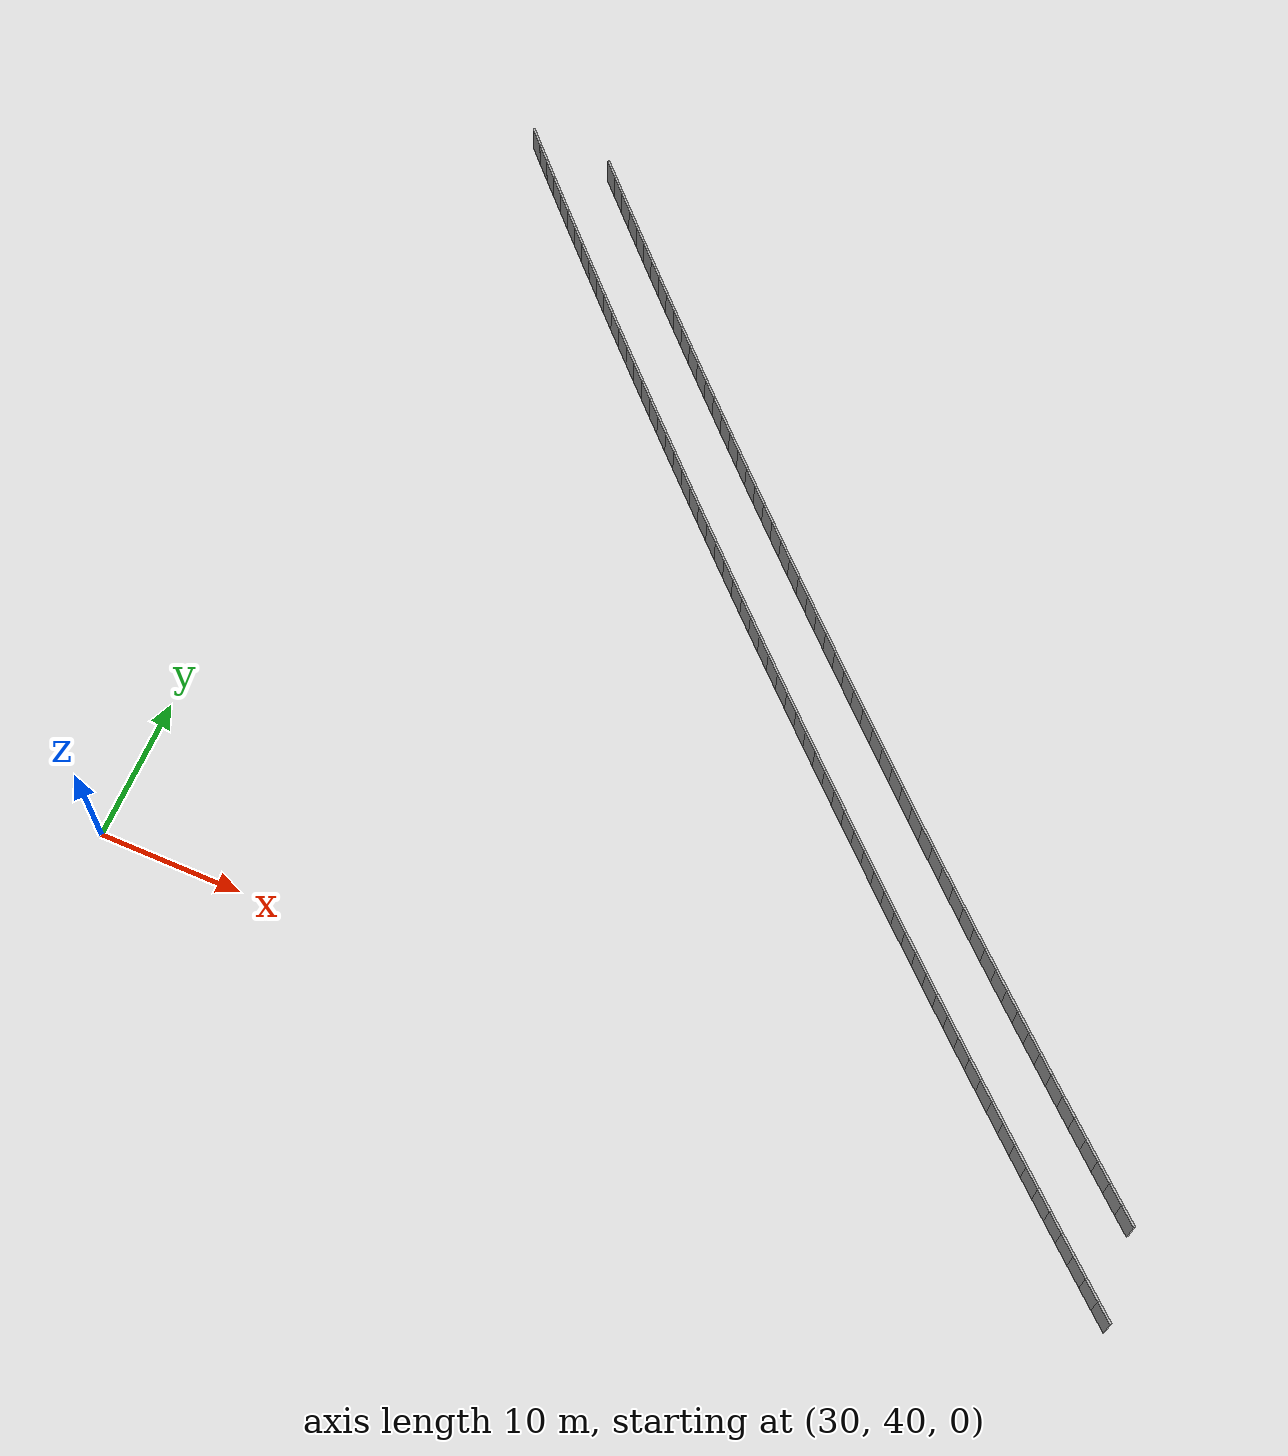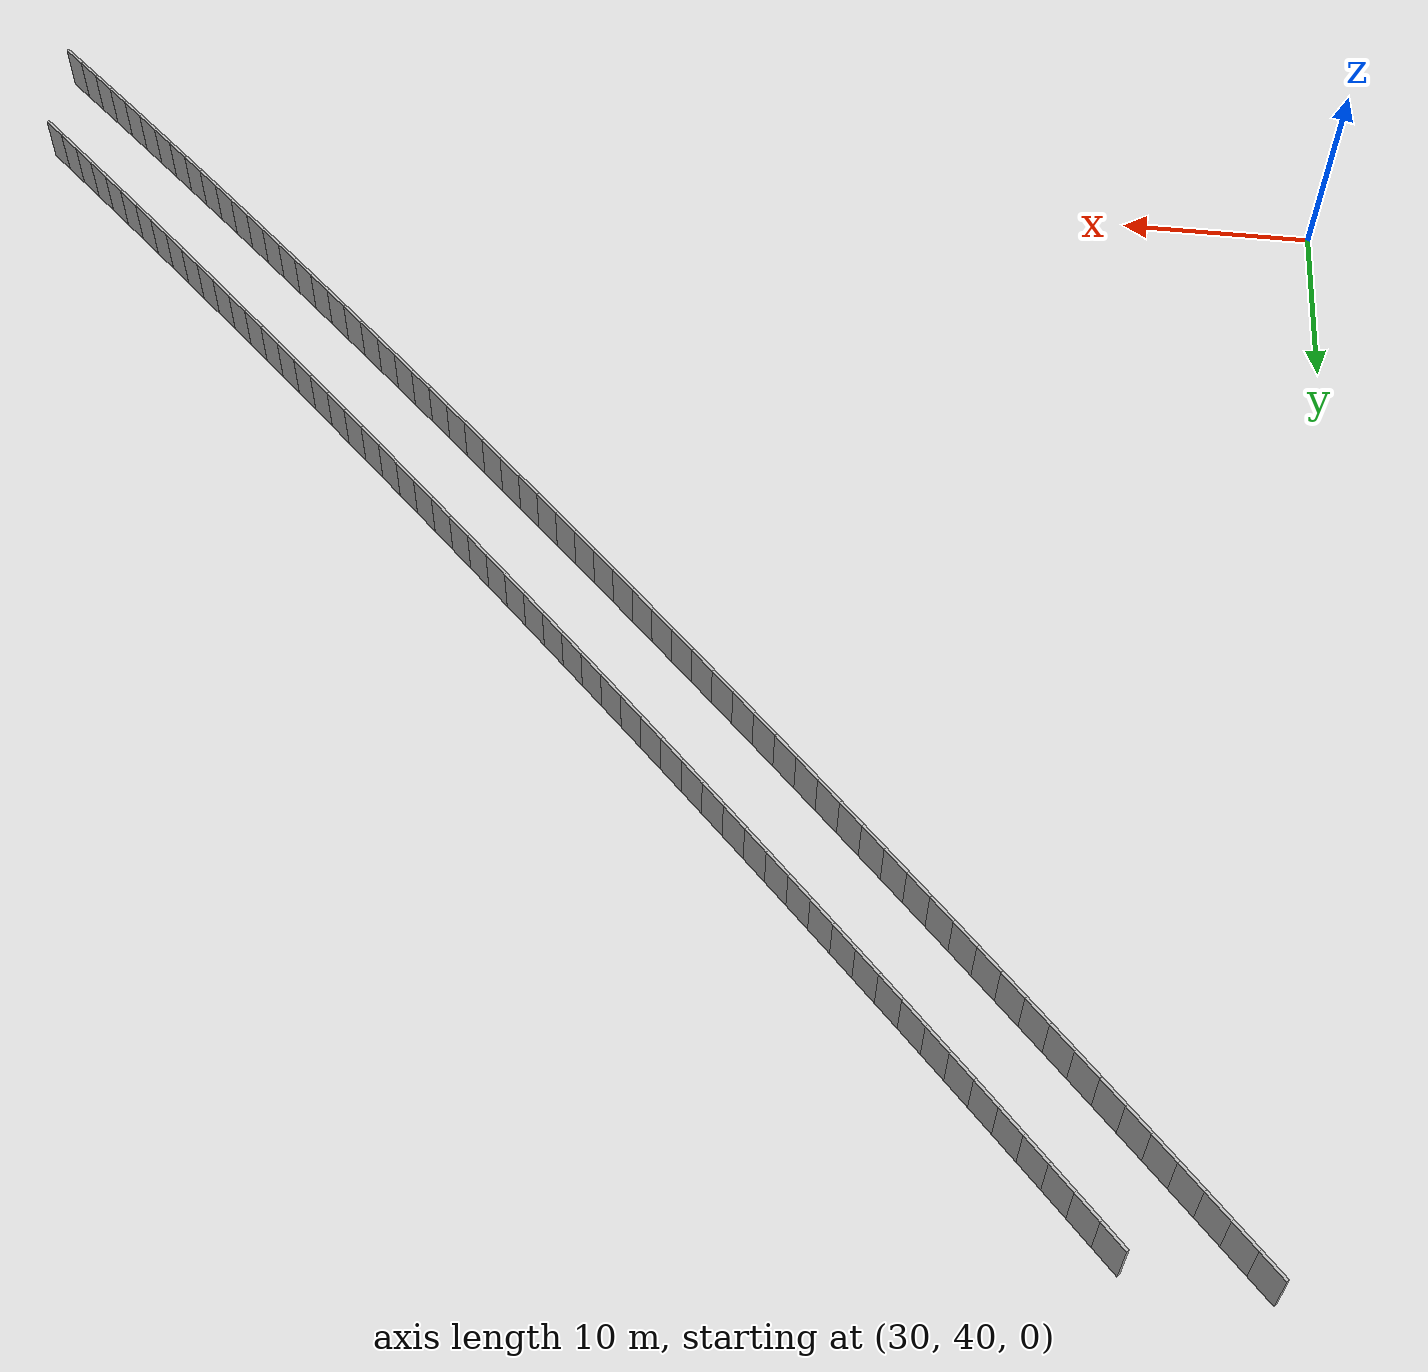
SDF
<?xml version="1.0" ?>
<sdf version="1.6">
  <model name="sps_0404">
    <pose frame="">0 0 0 0 -0 0</pose>
    <static>1</static>
    <self_collide>0</self_collide>
    <allow_auto_disable>0</allow_auto_disable>
    <link name="Wall8526">
      <kinematic>0</kinematic>
      <gravity>1</gravity>
      <self_collide>0</self_collide>
      <collision name="collision">
        <geometry>
          <box>
            <size>1.49906 0.15 2.5</size>
          </box>
        </geometry>
        <pose frame="">0 0 0 0 -0 0</pose>
      </collision>
      <visual name="visual">
        <geometry>
          <box>
            <size>1.49906 0.15 2.5</size>
          </box>
        </geometry>
        <pose frame="">0 0 0 0 -0 0</pose>
        <cast_shadows>1</cast_shadows>
        <transparency>0.0</transparency>
      </visual>
      <pose frame="">34.7833 99.8091 1.25 0 0 -0.826983</pose>
    </link>
    <link name="Wall8527">
      <kinematic>0</kinematic>
      <gravity>1</gravity>
      <self_collide>0</self_collide>
      <collision name="collision">
        <geometry>
          <box>
            <size>1.49888 0.15 2.5</size>
          </box>
        </geometry>
        <pose frame="">0 0 0 0 -0 0</pose>
      </collision>
      <visual name="visual">
        <geometry>
          <box>
            <size>1.49888 0.15 2.5</size>
          </box>
        </geometry>
        <pose frame="">0 0 0 0 -0 0</pose>
        <cast_shadows>1</cast_shadows>
        <transparency>0.0</transparency>
      </visual>
      <pose frame="">35.7992 98.7068 1.25 0 0 -0.825432</pose>
    </link>
    <link name="Wall8528">
      <kinematic>0</kinematic>
      <gravity>1</gravity>
      <self_collide>0</self_collide>
      <collision name="collision">
        <geometry>
          <box>
            <size>1.49901 0.15 2.5</size>
          </box>
        </geometry>
        <pose frame="">0 0 0 0 -0 0</pose>
      </collision>
      <visual name="visual">
        <geometry>
          <box>
            <size>1.49901 0.15 2.5</size>
          </box>
        </geometry>
        <pose frame="">0 0 0 0 -0 0</pose>
        <cast_shadows>1</cast_shadows>
        <transparency>0.0</transparency>
      </visual>
      <pose frame="">36.8166 97.6061 1.25 0 0 -0.823902</pose>
    </link>
    <link name="Wall8529">
      <kinematic>0</kinematic>
      <gravity>1</gravity>
      <self_collide>0</self_collide>
      <collision name="collision">
        <geometry>
          <box>
            <size>1.49896 0.15 2.5</size>
          </box>
        </geometry>
        <pose frame="">0 0 0 0 -0 0</pose>
      </collision>
      <visual name="visual">
        <geometry>
          <box>
            <size>1.49896 0.15 2.5</size>
          </box>
        </geometry>
        <pose frame="">0 0 0 0 -0 0</pose>
        <cast_shadows>1</cast_shadows>
        <transparency>0.0</transparency>
      </visual>
      <pose frame="">37.8359 96.507 1.25 0 0 -0.822203</pose>
    </link>
    <link name="Wall8530">
      <kinematic>0</kinematic>
      <gravity>1</gravity>
      <self_collide>0</self_collide>
      <collision name="collision">
        <geometry>
          <box>
            <size>1.49892 0.15 2.5</size>
          </box>
        </geometry>
        <pose frame="">0 0 0 0 -0 0</pose>
      </collision>
      <visual name="visual">
        <geometry>
          <box>
            <size>1.49892 0.15 2.5</size>
          </box>
        </geometry>
        <pose frame="">0 0 0 0 -0 0</pose>
        <cast_shadows>1</cast_shadows>
        <transparency>0.0</transparency>
      </visual>
      <pose frame="">38.857 95.4096 1.25 0 0 -0.820677</pose>
    </link>
    <link name="Wall8531">
      <kinematic>0</kinematic>
      <gravity>1</gravity>
      <self_collide>0</self_collide>
      <collision name="collision">
        <geometry>
          <box>
            <size>1.49906 0.15 2.5</size>
          </box>
        </geometry>
        <pose frame="">0 0 0 0 -0 0</pose>
      </collision>
      <visual name="visual">
        <geometry>
          <box>
            <size>1.49906 0.15 2.5</size>
          </box>
        </geometry>
        <pose frame="">0 0 0 0 -0 0</pose>
        <cast_shadows>1</cast_shadows>
        <transparency>0.0</transparency>
      </visual>
      <pose frame="">39.8797 94.3137 1.25 0 0 -0.819204</pose>
    </link>
    <link name="Wall8532">
      <kinematic>0</kinematic>
      <gravity>1</gravity>
      <self_collide>0</self_collide>
      <collision name="collision">
        <geometry>
          <box>
            <size>1.49885 0.15 2.5</size>
          </box>
        </geometry>
        <pose frame="">0 0 0 0 -0 0</pose>
      </collision>
      <visual name="visual">
        <geometry>
          <box>
            <size>1.49885 0.15 2.5</size>
          </box>
        </geometry>
        <pose frame="">0 0 0 0 -0 0</pose>
        <cast_shadows>1</cast_shadows>
        <transparency>0.0</transparency>
      </visual>
      <pose frame="">40.904 93.2194 1.25 0 0 -0.817567</pose>
    </link>
    <link name="Wall8533">
      <kinematic>0</kinematic>
      <gravity>1</gravity>
      <self_collide>0</self_collide>
      <collision name="collision">
        <geometry>
          <box>
            <size>1.4989 0.15 2.5</size>
          </box>
        </geometry>
        <pose frame="">0 0 0 0 -0 0</pose>
      </collision>
      <visual name="visual">
        <geometry>
          <box>
            <size>1.4989 0.15 2.5</size>
          </box>
        </geometry>
        <pose frame="">0 0 0 0 -0 0</pose>
        <cast_shadows>1</cast_shadows>
        <transparency>0.0</transparency>
      </visual>
      <pose frame="">41.9301 92.1268 1.25 0 0 -0.815981</pose>
    </link>
    <link name="Wall8534">
      <kinematic>0</kinematic>
      <gravity>1</gravity>
      <self_collide>0</self_collide>
      <collision name="collision">
        <geometry>
          <box>
            <size>1.499 0.15 2.5</size>
          </box>
        </geometry>
        <pose frame="">0 0 0 0 -0 0</pose>
      </collision>
      <visual name="visual">
        <geometry>
          <box>
            <size>1.499 0.15 2.5</size>
          </box>
        </geometry>
        <pose frame="">0 0 0 0 -0 0</pose>
        <cast_shadows>1</cast_shadows>
        <transparency>0.0</transparency>
      </visual>
      <pose frame="">42.958 91.0358 1.25 0 0 -0.814366</pose>
    </link>
    <link name="Wall8535">
      <kinematic>0</kinematic>
      <gravity>1</gravity>
      <self_collide>0</self_collide>
      <collision name="collision">
        <geometry>
          <box>
            <size>1.49876 0.15 2.5</size>
          </box>
        </geometry>
        <pose frame="">0 0 0 0 -0 0</pose>
      </collision>
      <visual name="visual">
        <geometry>
          <box>
            <size>1.49876 0.15 2.5</size>
          </box>
        </geometry>
        <pose frame="">0 0 0 0 -0 0</pose>
        <cast_shadows>1</cast_shadows>
        <transparency>0.0</transparency>
      </visual>
      <pose frame="">43.9876 89.9465 1.25 0 0 -0.812758</pose>
    </link>
    <link name="Wall8536">
      <kinematic>0</kinematic>
      <gravity>1</gravity>
      <self_collide>0</self_collide>
      <collision name="collision">
        <geometry>
          <box>
            <size>1.49913 0.15 2.5</size>
          </box>
        </geometry>
        <pose frame="">0 0 0 0 -0 0</pose>
      </collision>
      <visual name="visual">
        <geometry>
          <box>
            <size>1.49913 0.15 2.5</size>
          </box>
        </geometry>
        <pose frame="">0 0 0 0 -0 0</pose>
        <cast_shadows>1</cast_shadows>
        <transparency>0.0</transparency>
      </visual>
      <pose frame="">45.019 88.8588 1.25 0 0 -0.811138</pose>
    </link>
    <link name="Wall8537">
      <kinematic>0</kinematic>
      <gravity>1</gravity>
      <self_collide>0</self_collide>
      <collision name="collision">
        <geometry>
          <box>
            <size>1.49881 0.15 2.5</size>
          </box>
        </geometry>
        <pose frame="">0 0 0 0 -0 0</pose>
      </collision>
      <visual name="visual">
        <geometry>
          <box>
            <size>1.49881 0.15 2.5</size>
          </box>
        </geometry>
        <pose frame="">0 0 0 0 -0 0</pose>
        <cast_shadows>1</cast_shadows>
        <transparency>0.0</transparency>
      </visual>
      <pose frame="">46.0521 87.7727 1.25 0 0 -0.809646</pose>
    </link>
    <link name="Wall8538">
      <kinematic>0</kinematic>
      <gravity>1</gravity>
      <self_collide>0</self_collide>
      <collision name="collision">
        <geometry>
          <box>
            <size>1.49902 0.15 2.5</size>
          </box>
        </geometry>
        <pose frame="">0 0 0 0 -0 0</pose>
      </collision>
      <visual name="visual">
        <geometry>
          <box>
            <size>1.49902 0.15 2.5</size>
          </box>
        </geometry>
        <pose frame="">0 0 0 0 -0 0</pose>
        <cast_shadows>1</cast_shadows>
        <transparency>0.0</transparency>
      </visual>
      <pose frame="">47.0868 86.6882 1.25 0 0 -0.808145</pose>
    </link>
    <link name="Wall8539">
      <kinematic>0</kinematic>
      <gravity>1</gravity>
      <self_collide>0</self_collide>
      <collision name="collision">
        <geometry>
          <box>
            <size>1.49901 0.15 2.5</size>
          </box>
        </geometry>
        <pose frame="">0 0 0 0 -0 0</pose>
      </collision>
      <visual name="visual">
        <geometry>
          <box>
            <size>1.49901 0.15 2.5</size>
          </box>
        </geometry>
        <pose frame="">0 0 0 0 -0 0</pose>
        <cast_shadows>1</cast_shadows>
        <transparency>0.0</transparency>
      </visual>
      <pose frame="">48.1233 85.6053 1.25 0 0 -0.806446</pose>
    </link>
    <link name="Wall8540">
      <kinematic>0</kinematic>
      <gravity>1</gravity>
      <self_collide>0</self_collide>
      <collision name="collision">
        <geometry>
          <box>
            <size>1.49879 0.15 2.5</size>
          </box>
        </geometry>
        <pose frame="">0 0 0 0 -0 0</pose>
      </collision>
      <visual name="visual">
        <geometry>
          <box>
            <size>1.49879 0.15 2.5</size>
          </box>
        </geometry>
        <pose frame="">0 0 0 0 -0 0</pose>
        <cast_shadows>1</cast_shadows>
        <transparency>0.0</transparency>
      </visual>
      <pose frame="">49.1616 84.5242 1.25 0 0 -0.804836</pose>
    </link>
    <link name="Wall8541">
      <kinematic>0</kinematic>
      <gravity>1</gravity>
      <self_collide>0</self_collide>
      <collision name="collision">
        <geometry>
          <box>
            <size>1.49904 0.15 2.5</size>
          </box>
        </geometry>
        <pose frame="">0 0 0 0 -0 0</pose>
      </collision>
      <visual name="visual">
        <geometry>
          <box>
            <size>1.49904 0.15 2.5</size>
          </box>
        </geometry>
        <pose frame="">0 0 0 0 -0 0</pose>
        <cast_shadows>1</cast_shadows>
        <transparency>0.0</transparency>
      </visual>
      <pose frame="">50.2015 83.4447 1.25 0 0 -0.803307</pose>
    </link>
    <link name="Wall8542">
      <kinematic>0</kinematic>
      <gravity>1</gravity>
      <self_collide>0</self_collide>
      <collision name="collision">
        <geometry>
          <box>
            <size>1.49896 0.15 2.5</size>
          </box>
        </geometry>
        <pose frame="">0 0 0 0 -0 0</pose>
      </collision>
      <visual name="visual">
        <geometry>
          <box>
            <size>1.49896 0.15 2.5</size>
          </box>
        </geometry>
        <pose frame="">0 0 0 0 -0 0</pose>
        <cast_shadows>1</cast_shadows>
        <transparency>0.0</transparency>
      </visual>
      <pose frame="">51.2431 82.3667 1.25 0 0 -0.801839</pose>
    </link>
    <link name="Wall8543">
      <kinematic>0</kinematic>
      <gravity>1</gravity>
      <self_collide>0</self_collide>
      <collision name="collision">
        <geometry>
          <box>
            <size>1.49879 0.15 2.5</size>
          </box>
        </geometry>
        <pose frame="">0 0 0 0 -0 0</pose>
      </collision>
      <visual name="visual">
        <geometry>
          <box>
            <size>1.49879 0.15 2.5</size>
          </box>
        </geometry>
        <pose frame="">0 0 0 0 -0 0</pose>
        <cast_shadows>1</cast_shadows>
        <transparency>0.0</transparency>
      </visual>
      <pose frame="">52.2863 81.2905 1.25 0 0 -0.800027</pose>
    </link>
    <link name="Wall8544">
      <kinematic>0</kinematic>
      <gravity>1</gravity>
      <self_collide>0</self_collide>
      <collision name="collision">
        <geometry>
          <box>
            <size>1.49893 0.15 2.5</size>
          </box>
        </geometry>
        <pose frame="">0 0 0 0 -0 0</pose>
      </collision>
      <visual name="visual">
        <geometry>
          <box>
            <size>1.49893 0.15 2.5</size>
          </box>
        </geometry>
        <pose frame="">0 0 0 0 -0 0</pose>
        <cast_shadows>1</cast_shadows>
        <transparency>0.0</transparency>
      </visual>
      <pose frame="">53.3314 80.216 1.25 0 0 -0.798586</pose>
    </link>
    <link name="Wall8545">
      <kinematic>0</kinematic>
      <gravity>1</gravity>
      <self_collide>0</self_collide>
      <collision name="collision">
        <geometry>
          <box>
            <size>1.49903 0.15 2.5</size>
          </box>
        </geometry>
        <pose frame="">0 0 0 0 -0 0</pose>
      </collision>
      <visual name="visual">
        <geometry>
          <box>
            <size>1.49903 0.15 2.5</size>
          </box>
        </geometry>
        <pose frame="">0 0 0 0 -0 0</pose>
        <cast_shadows>1</cast_shadows>
        <transparency>0.0</transparency>
      </visual>
      <pose frame="">54.3781 79.143 1.25 0 0 -0.797001</pose>
    </link>
    <link name="Wall8546">
      <kinematic>0</kinematic>
      <gravity>1</gravity>
      <self_collide>0</self_collide>
      <collision name="collision">
        <geometry>
          <box>
            <size>1.49896 0.15 2.5</size>
          </box>
        </geometry>
        <pose frame="">0 0 0 0 -0 0</pose>
      </collision>
      <visual name="visual">
        <geometry>
          <box>
            <size>1.49896 0.15 2.5</size>
          </box>
        </geometry>
        <pose frame="">0 0 0 0 -0 0</pose>
        <cast_shadows>1</cast_shadows>
        <transparency>0.0</transparency>
      </visual>
      <pose frame="">55.4266 78.0717 1.25 0 0 -0.795303</pose>
    </link>
    <link name="Wall8547">
      <kinematic>0</kinematic>
      <gravity>1</gravity>
      <self_collide>0</self_collide>
      <collision name="collision">
        <geometry>
          <box>
            <size>1.49886 0.15 2.5</size>
          </box>
        </geometry>
        <pose frame="">0 0 0 0 -0 0</pose>
      </collision>
      <visual name="visual">
        <geometry>
          <box>
            <size>1.49886 0.15 2.5</size>
          </box>
        </geometry>
        <pose frame="">0 0 0 0 -0 0</pose>
        <cast_shadows>1</cast_shadows>
        <transparency>0.0</transparency>
      </visual>
      <pose frame="">56.4766 77.0021 1.25 0 0 -0.793921</pose>
    </link>
    <link name="Wall8548">
      <kinematic>0</kinematic>
      <gravity>1</gravity>
      <self_collide>0</self_collide>
      <collision name="collision">
        <geometry>
          <box>
            <size>1.49897 0.15 2.5</size>
          </box>
        </geometry>
        <pose frame="">0 0 0 0 -0 0</pose>
      </collision>
      <visual name="visual">
        <geometry>
          <box>
            <size>1.49897 0.15 2.5</size>
          </box>
        </geometry>
        <pose frame="">0 0 0 0 -0 0</pose>
        <cast_shadows>1</cast_shadows>
        <transparency>0.0</transparency>
      </visual>
      <pose frame="">57.5283 75.9341 1.25 0 0 -0.79228</pose>
    </link>
    <link name="Wall8549">
      <kinematic>0</kinematic>
      <gravity>1</gravity>
      <self_collide>0</self_collide>
      <collision name="collision">
        <geometry>
          <box>
            <size>1.49904 0.15 2.5</size>
          </box>
        </geometry>
        <pose frame="">0 0 0 0 -0 0</pose>
      </collision>
      <visual name="visual">
        <geometry>
          <box>
            <size>1.49904 0.15 2.5</size>
          </box>
        </geometry>
        <pose frame="">0 0 0 0 -0 0</pose>
        <cast_shadows>1</cast_shadows>
        <transparency>0.0</transparency>
      </visual>
      <pose frame="">58.5818 74.8677 1.25 0 0 -0.790667</pose>
    </link>
    <link name="Wall8550">
      <kinematic>0</kinematic>
      <gravity>1</gravity>
      <self_collide>0</self_collide>
      <collision name="collision">
        <geometry>
          <box>
            <size>1.49899 0.15 2.5</size>
          </box>
        </geometry>
        <pose frame="">0 0 0 0 -0 0</pose>
      </collision>
      <visual name="visual">
        <geometry>
          <box>
            <size>1.49899 0.15 2.5</size>
          </box>
        </geometry>
        <pose frame="">0 0 0 0 -0 0</pose>
        <cast_shadows>1</cast_shadows>
        <transparency>0.0</transparency>
      </visual>
      <pose frame="">59.637 73.803 1.25 0 0 -0.789084</pose>
    </link>
    <link name="Wall8551">
      <kinematic>0</kinematic>
      <gravity>1</gravity>
      <self_collide>0</self_collide>
      <collision name="collision">
        <geometry>
          <box>
            <size>1.49894 0.15 2.5</size>
          </box>
        </geometry>
        <pose frame="">0 0 0 0 -0 0</pose>
      </collision>
      <visual name="visual">
        <geometry>
          <box>
            <size>1.49894 0.15 2.5</size>
          </box>
        </geometry>
        <pose frame="">0 0 0 0 -0 0</pose>
        <cast_shadows>1</cast_shadows>
        <transparency>0.0</transparency>
      </visual>
      <pose frame="">60.6939 72.74 1.25 0 0 -0.787558</pose>
    </link>
    <link name="Wall8552">
      <kinematic>0</kinematic>
      <gravity>1</gravity>
      <self_collide>0</self_collide>
      <collision name="collision">
        <geometry>
          <box>
            <size>1.49906 0.15 2.5</size>
          </box>
        </geometry>
        <pose frame="">0 0 0 0 -0 0</pose>
      </collision>
      <visual name="visual">
        <geometry>
          <box>
            <size>1.49906 0.15 2.5</size>
          </box>
        </geometry>
        <pose frame="">0 0 0 0 -0 0</pose>
        <cast_shadows>1</cast_shadows>
        <transparency>0.0</transparency>
      </visual>
      <pose frame="">61.7524 71.6786 1.25 0 0 -0.785974</pose>
    </link>
    <link name="Wall8553">
      <kinematic>0</kinematic>
      <gravity>1</gravity>
      <self_collide>0</self_collide>
      <collision name="collision">
        <geometry>
          <box>
            <size>1.49876 0.15 2.5</size>
          </box>
        </geometry>
        <pose frame="">0 0 0 0 -0 0</pose>
      </collision>
      <visual name="visual">
        <geometry>
          <box>
            <size>1.49876 0.15 2.5</size>
          </box>
        </geometry>
        <pose frame="">0 0 0 0 -0 0</pose>
        <cast_shadows>1</cast_shadows>
        <transparency>0.0</transparency>
      </visual>
      <pose frame="">62.8126 70.619 1.25 0 0 -0.784275</pose>
    </link>
    <link name="Wall8554">
      <kinematic>0</kinematic>
      <gravity>1</gravity>
      <self_collide>0</self_collide>
      <collision name="collision">
        <geometry>
          <box>
            <size>1.49894 0.15 2.5</size>
          </box>
        </geometry>
        <pose frame="">0 0 0 0 -0 0</pose>
      </collision>
      <visual name="visual">
        <geometry>
          <box>
            <size>1.49894 0.15 2.5</size>
          </box>
        </geometry>
        <pose frame="">0 0 0 0 -0 0</pose>
        <cast_shadows>1</cast_shadows>
        <transparency>0.0</transparency>
      </visual>
      <pose frame="">63.8744 69.5611 1.25 0 0 -0.782836</pose>
    </link>
    <link name="Wall8555">
      <kinematic>0</kinematic>
      <gravity>1</gravity>
      <self_collide>0</self_collide>
      <collision name="collision">
        <geometry>
          <box>
            <size>1.49895 0.15 2.5</size>
          </box>
        </geometry>
        <pose frame="">0 0 0 0 -0 0</pose>
      </collision>
      <visual name="visual">
        <geometry>
          <box>
            <size>1.49895 0.15 2.5</size>
          </box>
        </geometry>
        <pose frame="">0 0 0 0 -0 0</pose>
        <cast_shadows>1</cast_shadows>
        <transparency>0.0</transparency>
      </visual>
      <pose frame="">64.9379 68.5048 1.25 0 0 -0.781166</pose>
    </link>
    <link name="Wall8556">
      <kinematic>0</kinematic>
      <gravity>1</gravity>
      <self_collide>0</self_collide>
      <collision name="collision">
        <geometry>
          <box>
            <size>1.49892 0.15 2.5</size>
          </box>
        </geometry>
        <pose frame="">0 0 0 0 -0 0</pose>
      </collision>
      <visual name="visual">
        <geometry>
          <box>
            <size>1.49892 0.15 2.5</size>
          </box>
        </geometry>
        <pose frame="">0 0 0 0 -0 0</pose>
        <cast_shadows>1</cast_shadows>
        <transparency>0.0</transparency>
      </visual>
      <pose frame="">66.003 67.4502 1.25 0 0 -0.77964</pose>
    </link>
    <link name="Wall8557">
      <kinematic>0</kinematic>
      <gravity>1</gravity>
      <self_collide>0</self_collide>
      <collision name="collision">
        <geometry>
          <box>
            <size>1.49898 0.15 2.5</size>
          </box>
        </geometry>
        <pose frame="">0 0 0 0 -0 0</pose>
      </collision>
      <visual name="visual">
        <geometry>
          <box>
            <size>1.49898 0.15 2.5</size>
          </box>
        </geometry>
        <pose frame="">0 0 0 0 -0 0</pose>
        <cast_shadows>1</cast_shadows>
        <transparency>0.0</transparency>
      </visual>
      <pose frame="">67.0699 66.3973 1.25 0 0 -0.777941</pose>
    </link>
    <link name="Wall8558">
      <kinematic>0</kinematic>
      <gravity>1</gravity>
      <self_collide>0</self_collide>
      <collision name="collision">
        <geometry>
          <box>
            <size>1.49899 0.15 2.5</size>
          </box>
        </geometry>
        <pose frame="">0 0 0 0 -0 0</pose>
      </collision>
      <visual name="visual">
        <geometry>
          <box>
            <size>1.49899 0.15 2.5</size>
          </box>
        </geometry>
        <pose frame="">0 0 0 0 -0 0</pose>
        <cast_shadows>1</cast_shadows>
        <transparency>0.0</transparency>
      </visual>
      <pose frame="">68.1385 65.3461 1.25 0 0 -0.776444</pose>
    </link>
    <link name="Wall8559">
      <kinematic>0</kinematic>
      <gravity>1</gravity>
      <self_collide>0</self_collide>
      <collision name="collision">
        <geometry>
          <box>
            <size>1.49884 0.15 2.5</size>
          </box>
        </geometry>
        <pose frame="">0 0 0 0 -0 0</pose>
      </collision>
      <visual name="visual">
        <geometry>
          <box>
            <size>1.49884 0.15 2.5</size>
          </box>
        </geometry>
        <pose frame="">0 0 0 0 -0 0</pose>
        <cast_shadows>1</cast_shadows>
        <transparency>0.0</transparency>
      </visual>
      <pose frame="">69.2086 64.2965 1.25 0 0 -0.775003</pose>
    </link>
    <link name="Wall8560">
      <kinematic>0</kinematic>
      <gravity>1</gravity>
      <self_collide>0</self_collide>
      <collision name="collision">
        <geometry>
          <box>
            <size>1.49904 0.15 2.5</size>
          </box>
        </geometry>
        <pose frame="">0 0 0 0 -0 0</pose>
      </collision>
      <visual name="visual">
        <geometry>
          <box>
            <size>1.49904 0.15 2.5</size>
          </box>
        </geometry>
        <pose frame="">0 0 0 0 -0 0</pose>
        <cast_shadows>1</cast_shadows>
        <transparency>0.0</transparency>
      </visual>
      <pose frame="">70.2804 63.2486 1.25 0 0 -0.773219</pose>
    </link>
    <link name="Wall8561">
      <kinematic>0</kinematic>
      <gravity>1</gravity>
      <self_collide>0</self_collide>
      <collision name="collision">
        <geometry>
          <box>
            <size>1.49881 0.15 2.5</size>
          </box>
        </geometry>
        <pose frame="">0 0 0 0 -0 0</pose>
      </collision>
      <visual name="visual">
        <geometry>
          <box>
            <size>1.49881 0.15 2.5</size>
          </box>
        </geometry>
        <pose frame="">0 0 0 0 -0 0</pose>
        <cast_shadows>1</cast_shadows>
        <transparency>0.0</transparency>
      </visual>
      <pose frame="">71.354 62.2025 1.25 0 0 -0.77172</pose>
    </link>
    <link name="Wall8562">
      <kinematic>0</kinematic>
      <gravity>1</gravity>
      <self_collide>0</self_collide>
      <collision name="collision">
        <geometry>
          <box>
            <size>1.49906 0.15 2.5</size>
          </box>
        </geometry>
        <pose frame="">0 0 0 0 -0 0</pose>
      </collision>
      <visual name="visual">
        <geometry>
          <box>
            <size>1.49906 0.15 2.5</size>
          </box>
        </geometry>
        <pose frame="">0 0 0 0 -0 0</pose>
        <cast_shadows>1</cast_shadows>
        <transparency>0.0</transparency>
      </visual>
      <pose frame="">72.4291 61.158 1.25 0 0 -0.770196</pose>
    </link>
    <link name="Wall8563">
      <kinematic>0</kinematic>
      <gravity>1</gravity>
      <self_collide>0</self_collide>
      <collision name="collision">
        <geometry>
          <box>
            <size>1.49884 0.15 2.5</size>
          </box>
        </geometry>
        <pose frame="">0 0 0 0 -0 0</pose>
      </collision>
      <visual name="visual">
        <geometry>
          <box>
            <size>1.49884 0.15 2.5</size>
          </box>
        </geometry>
        <pose frame="">0 0 0 0 -0 0</pose>
        <cast_shadows>1</cast_shadows>
        <transparency>0.0</transparency>
      </visual>
      <pose frame="">73.5059 60.1152 1.25 0 0 -0.768524</pose>
    </link>
    <link name="Wall8564">
      <kinematic>0</kinematic>
      <gravity>1</gravity>
      <self_collide>0</self_collide>
      <collision name="collision">
        <geometry>
          <box>
            <size>1.49893 0.15 2.5</size>
          </box>
        </geometry>
        <pose frame="">0 0 0 0 -0 0</pose>
      </collision>
      <visual name="visual">
        <geometry>
          <box>
            <size>1.49893 0.15 2.5</size>
          </box>
        </geometry>
        <pose frame="">0 0 0 0 -0 0</pose>
        <cast_shadows>1</cast_shadows>
        <transparency>0.0</transparency>
      </visual>
      <pose frame="">74.5843 59.0742 1.25 0 0 -0.766999</pose>
    </link>
    <link name="Wall8565">
      <kinematic>0</kinematic>
      <gravity>1</gravity>
      <self_collide>0</self_collide>
      <collision name="collision">
        <geometry>
          <box>
            <size>1.49906 0.15 2.5</size>
          </box>
        </geometry>
        <pose frame="">0 0 0 0 -0 0</pose>
      </collision>
      <visual name="visual">
        <geometry>
          <box>
            <size>1.49906 0.15 2.5</size>
          </box>
        </geometry>
        <pose frame="">0 0 0 0 -0 0</pose>
        <cast_shadows>1</cast_shadows>
        <transparency>0.0</transparency>
      </visual>
      <pose frame="">75.6644 58.0348 1.25 0 0 -0.765388</pose>
    </link>
    <link name="Wall8566">
      <kinematic>0</kinematic>
      <gravity>1</gravity>
      <self_collide>0</self_collide>
      <collision name="collision">
        <geometry>
          <box>
            <size>1.49898 0.15 2.5</size>
          </box>
        </geometry>
        <pose frame="">0 0 0 0 -0 0</pose>
      </collision>
      <visual name="visual">
        <geometry>
          <box>
            <size>1.49898 0.15 2.5</size>
          </box>
        </geometry>
        <pose frame="">0 0 0 0 -0 0</pose>
        <cast_shadows>1</cast_shadows>
        <transparency>0.0</transparency>
      </visual>
      <pose frame="">76.7461 56.9971 1.25 0 0 -0.763803</pose>
    </link>
    <link name="Wall8567">
      <kinematic>0</kinematic>
      <gravity>1</gravity>
      <self_collide>0</self_collide>
      <collision name="collision">
        <geometry>
          <box>
            <size>1.49882 0.15 2.5</size>
          </box>
        </geometry>
        <pose frame="">0 0 0 0 -0 0</pose>
      </collision>
      <visual name="visual">
        <geometry>
          <box>
            <size>1.49882 0.15 2.5</size>
          </box>
        </geometry>
        <pose frame="">0 0 0 0 -0 0</pose>
        <cast_shadows>1</cast_shadows>
        <transparency>0.0</transparency>
      </visual>
      <pose frame="">77.8295 55.9612 1.25 0 0 -0.762274</pose>
    </link>
    <link name="Wall8568">
      <kinematic>0</kinematic>
      <gravity>1</gravity>
      <self_collide>0</self_collide>
      <collision name="collision">
        <geometry>
          <box>
            <size>1.49892 0.15 2.5</size>
          </box>
        </geometry>
        <pose frame="">0 0 0 0 -0 0</pose>
      </collision>
      <visual name="visual">
        <geometry>
          <box>
            <size>1.49892 0.15 2.5</size>
          </box>
        </geometry>
        <pose frame="">0 0 0 0 -0 0</pose>
        <cast_shadows>1</cast_shadows>
        <transparency>0.0</transparency>
      </visual>
      <pose frame="">78.9144 54.927 1.25 0 0 -0.760691</pose>
    </link>
    <link name="Wall8569">
      <kinematic>0</kinematic>
      <gravity>1</gravity>
      <self_collide>0</self_collide>
      <collision name="collision">
        <geometry>
          <box>
            <size>1.49889 0.15 2.5</size>
          </box>
        </geometry>
        <pose frame="">0 0 0 0 -0 0</pose>
      </collision>
      <visual name="visual">
        <geometry>
          <box>
            <size>1.49889 0.15 2.5</size>
          </box>
        </geometry>
        <pose frame="">0 0 0 0 -0 0</pose>
        <cast_shadows>1</cast_shadows>
        <transparency>0.0</transparency>
      </visual>
      <pose frame="">80.0009 53.8945 1.25 0 0 -0.759078</pose>
    </link>
    <link name="Wall8570">
      <kinematic>0</kinematic>
      <gravity>1</gravity>
      <self_collide>0</self_collide>
      <collision name="collision">
        <geometry>
          <box>
            <size>1.49896 0.15 2.5</size>
          </box>
        </geometry>
        <pose frame="">0 0 0 0 -0 0</pose>
      </collision>
      <visual name="visual">
        <geometry>
          <box>
            <size>1.49896 0.15 2.5</size>
          </box>
        </geometry>
        <pose frame="">0 0 0 0 -0 0</pose>
        <cast_shadows>1</cast_shadows>
        <transparency>0.0</transparency>
      </visual>
      <pose frame="">81.0893 52.8638 1.25 0 0 -0.757351</pose>
    </link>
    <link name="Wall8571">
      <kinematic>0</kinematic>
      <gravity>1</gravity>
      <self_collide>0</self_collide>
      <collision name="collision">
        <geometry>
          <box>
            <size>1.49885 0.15 2.5</size>
          </box>
        </geometry>
        <pose frame="">0 0 0 0 -0 0</pose>
      </collision>
      <visual name="visual">
        <geometry>
          <box>
            <size>1.49885 0.15 2.5</size>
          </box>
        </geometry>
        <pose frame="">0 0 0 0 -0 0</pose>
        <cast_shadows>1</cast_shadows>
        <transparency>0.0</transparency>
      </visual>
      <pose frame="">82.1792 51.8348 1.25 0 0 -0.755966</pose>
    </link>
    <link name="Wall8572">
      <kinematic>0</kinematic>
      <gravity>1</gravity>
      <self_collide>0</self_collide>
      <collision name="collision">
        <geometry>
          <box>
            <size>1.49909 0.15 2.5</size>
          </box>
        </geometry>
        <pose frame="">0 0 0 0 -0 0</pose>
      </collision>
      <visual name="visual">
        <geometry>
          <box>
            <size>1.49909 0.15 2.5</size>
          </box>
        </geometry>
        <pose frame="">0 0 0 0 -0 0</pose>
        <cast_shadows>1</cast_shadows>
        <transparency>0.0</transparency>
      </visual>
      <pose frame="">83.2707 50.8074 1.25 0 0 -0.754358</pose>
    </link>
    <link name="Wall8573">
      <kinematic>0</kinematic>
      <gravity>1</gravity>
      <self_collide>0</self_collide>
      <collision name="collision">
        <geometry>
          <box>
            <size>1.49887 0.15 2.5</size>
          </box>
        </geometry>
        <pose frame="">0 0 0 0 -0 0</pose>
      </collision>
      <visual name="visual">
        <geometry>
          <box>
            <size>1.49887 0.15 2.5</size>
          </box>
        </geometry>
        <pose frame="">0 0 0 0 -0 0</pose>
        <cast_shadows>1</cast_shadows>
        <transparency>0.0</transparency>
      </visual>
      <pose frame="">84.3639 49.7818 1.25 0 0 -0.752654</pose>
    </link>
    <link name="Wall8574">
      <kinematic>0</kinematic>
      <gravity>1</gravity>
      <self_collide>0</self_collide>
      <collision name="collision">
        <geometry>
          <box>
            <size>1.49882 0.15 2.5</size>
          </box>
        </geometry>
        <pose frame="">0 0 0 0 -0 0</pose>
      </collision>
      <visual name="visual">
        <geometry>
          <box>
            <size>1.49882 0.15 2.5</size>
          </box>
        </geometry>
        <pose frame="">0 0 0 0 -0 0</pose>
        <cast_shadows>1</cast_shadows>
        <transparency>0.0</transparency>
      </visual>
      <pose frame="">85.4585 48.758 1.25 0 0 -0.751241</pose>
    </link>
    <link name="Wall8575">
      <kinematic>0</kinematic>
      <gravity>1</gravity>
      <self_collide>0</self_collide>
      <collision name="collision">
        <geometry>
          <box>
            <size>1.49903 0.15 2.5</size>
          </box>
        </geometry>
        <pose frame="">0 0 0 0 -0 0</pose>
      </collision>
      <visual name="visual">
        <geometry>
          <box>
            <size>1.49903 0.15 2.5</size>
          </box>
        </geometry>
        <pose frame="">0 0 0 0 -0 0</pose>
        <cast_shadows>1</cast_shadows>
        <transparency>0.0</transparency>
      </visual>
      <pose frame="">86.5549 47.7358 1.25 0 0 -0.749603</pose>
    </link>
    <link name="Wall8576">
      <kinematic>0</kinematic>
      <gravity>1</gravity>
      <self_collide>0</self_collide>
      <collision name="collision">
        <geometry>
          <box>
            <size>1.49894 0.15 2.5</size>
          </box>
        </geometry>
        <pose frame="">0 0 0 0 -0 0</pose>
      </collision>
      <visual name="visual">
        <geometry>
          <box>
            <size>1.49894 0.15 2.5</size>
          </box>
        </geometry>
        <pose frame="">0 0 0 0 -0 0</pose>
        <cast_shadows>1</cast_shadows>
        <transparency>0.0</transparency>
      </visual>
      <pose frame="">87.6529 46.7153 1.25 0 0 -0.748046</pose>
    </link>
    <link name="Wall8577">
      <kinematic>0</kinematic>
      <gravity>1</gravity>
      <self_collide>0</self_collide>
      <collision name="collision">
        <geometry>
          <box>
            <size>1.49895 0.15 2.5</size>
          </box>
        </geometry>
        <pose frame="">0 0 0 0 -0 0</pose>
      </collision>
      <visual name="visual">
        <geometry>
          <box>
            <size>1.49895 0.15 2.5</size>
          </box>
        </geometry>
        <pose frame="">0 0 0 0 -0 0</pose>
        <cast_shadows>1</cast_shadows>
        <transparency>0.0</transparency>
      </visual>
      <pose frame="">88.7524 45.6966 1.25 0 0 -0.746432</pose>
    </link>
    <link name="Wall8578">
      <kinematic>0</kinematic>
      <gravity>1</gravity>
      <self_collide>0</self_collide>
      <collision name="collision">
        <geometry>
          <box>
            <size>1.49892 0.15 2.5</size>
          </box>
        </geometry>
        <pose frame="">0 0 0 0 -0 0</pose>
      </collision>
      <visual name="visual">
        <geometry>
          <box>
            <size>1.49892 0.15 2.5</size>
          </box>
        </geometry>
        <pose frame="">0 0 0 0 -0 0</pose>
        <cast_shadows>1</cast_shadows>
        <transparency>0.0</transparency>
      </visual>
      <pose frame="">89.8537 44.6797 1.25 0 0 -0.744789</pose>
    </link>
    <link name="Wall8579">
      <kinematic>0</kinematic>
      <gravity>1</gravity>
      <self_collide>0</self_collide>
      <collision name="collision">
        <geometry>
          <box>
            <size>1.49897 0.15 2.5</size>
          </box>
        </geometry>
        <pose frame="">0 0 0 0 -0 0</pose>
      </collision>
      <visual name="visual">
        <geometry>
          <box>
            <size>1.49897 0.15 2.5</size>
          </box>
        </geometry>
        <pose frame="">0 0 0 0 -0 0</pose>
        <cast_shadows>1</cast_shadows>
        <transparency>0.0</transparency>
      </visual>
      <pose frame="">90.9565 43.6645 1.25 0 0 -0.74332</pose>
    </link>
    <link name="Wall8580">
      <kinematic>0</kinematic>
      <gravity>1</gravity>
      <self_collide>0</self_collide>
      <collision name="collision">
        <geometry>
          <box>
            <size>1.49894 0.15 2.5</size>
          </box>
        </geometry>
        <pose frame="">0 0 0 0 -0 0</pose>
      </collision>
      <visual name="visual">
        <geometry>
          <box>
            <size>1.49894 0.15 2.5</size>
          </box>
        </geometry>
        <pose frame="">0 0 0 0 -0 0</pose>
        <cast_shadows>1</cast_shadows>
        <transparency>0.0</transparency>
      </visual>
      <pose frame="">92.0608 42.651 1.25 0 0 -0.741735</pose>
    </link>
    <link name="Wall8581">
      <kinematic>0</kinematic>
      <gravity>1</gravity>
      <self_collide>0</self_collide>
      <collision name="collision">
        <geometry>
          <box>
            <size>1.49892 0.15 2.5</size>
          </box>
        </geometry>
        <pose frame="">0 0 0 0 -0 0</pose>
      </collision>
      <visual name="visual">
        <geometry>
          <box>
            <size>1.49892 0.15 2.5</size>
          </box>
        </geometry>
        <pose frame="">0 0 0 0 -0 0</pose>
        <cast_shadows>1</cast_shadows>
        <transparency>0.0</transparency>
      </visual>
      <pose frame="">93.1668 41.6393 1.25 0 0 -0.740091</pose>
    </link>
    <link name="Wall8582">
      <kinematic>0</kinematic>
      <gravity>1</gravity>
      <self_collide>0</self_collide>
      <collision name="collision">
        <geometry>
          <box>
            <size>1.49898 0.15 2.5</size>
          </box>
        </geometry>
        <pose frame="">0 0 0 0 -0 0</pose>
      </collision>
      <visual name="visual">
        <geometry>
          <box>
            <size>1.49898 0.15 2.5</size>
          </box>
        </geometry>
        <pose frame="">0 0 0 0 -0 0</pose>
        <cast_shadows>1</cast_shadows>
        <transparency>0.0</transparency>
      </visual>
      <pose frame="">94.2744 40.6293 1.25 0 0 -0.738566</pose>
    </link>
    <link name="Wall8583">
      <kinematic>0</kinematic>
      <gravity>1</gravity>
      <self_collide>0</self_collide>
      <collision name="collision">
        <geometry>
          <box>
            <size>1.49889 0.15 2.5</size>
          </box>
        </geometry>
        <pose frame="">0 0 0 0 -0 0</pose>
      </collision>
      <visual name="visual">
        <geometry>
          <box>
            <size>1.49889 0.15 2.5</size>
          </box>
        </geometry>
        <pose frame="">0 0 0 0 -0 0</pose>
        <cast_shadows>1</cast_shadows>
        <transparency>0.0</transparency>
      </visual>
      <pose frame="">95.3837 39.6211 1.25 0 0 -0.736862</pose>
    </link>
    <link name="Wall8584">
      <kinematic>0</kinematic>
      <gravity>1</gravity>
      <self_collide>0</self_collide>
      <collision name="collision">
        <geometry>
          <box>
            <size>1.49895 0.15 2.5</size>
          </box>
        </geometry>
        <pose frame="">0 0 0 0 -0 0</pose>
      </collision>
      <visual name="visual">
        <geometry>
          <box>
            <size>1.49895 0.15 2.5</size>
          </box>
        </geometry>
        <pose frame="">0 0 0 0 -0 0</pose>
        <cast_shadows>1</cast_shadows>
        <transparency>0.0</transparency>
      </visual>
      <pose frame="">96.4945 38.6147 1.25 0 0 -0.735394</pose>
    </link>
    <link name="Wall8585">
      <kinematic>0</kinematic>
      <gravity>1</gravity>
      <self_collide>0</self_collide>
      <collision name="collision">
        <geometry>
          <box>
            <size>1.49895 0.15 2.5</size>
          </box>
        </geometry>
        <pose frame="">0 0 0 0 -0 0</pose>
      </collision>
      <visual name="visual">
        <geometry>
          <box>
            <size>1.49895 0.15 2.5</size>
          </box>
        </geometry>
        <pose frame="">0 0 0 0 -0 0</pose>
        <cast_shadows>1</cast_shadows>
        <transparency>0.0</transparency>
      </visual>
      <pose frame="">97.6069 37.61 1.25 0 0 -0.73375</pose>
    </link>
    <link name="Wall8586">
      <kinematic>0</kinematic>
      <gravity>1</gravity>
      <self_collide>0</self_collide>
      <collision name="collision">
        <geometry>
          <box>
            <size>1.49906 0.15 2.5</size>
          </box>
        </geometry>
        <pose frame="">0 0 0 0 -0 0</pose>
      </collision>
      <visual name="visual">
        <geometry>
          <box>
            <size>1.49906 0.15 2.5</size>
          </box>
        </geometry>
        <pose frame="">0 0 0 0 -0 0</pose>
        <cast_shadows>1</cast_shadows>
        <transparency>0.0</transparency>
      </visual>
      <pose frame="">98.7209 36.607 1.25 0 0 -0.732255</pose>
    </link>
    <link name="Wall8587">
      <kinematic>0</kinematic>
      <gravity>1</gravity>
      <self_collide>0</self_collide>
      <collision name="collision">
        <geometry>
          <box>
            <size>1.49876 0.15 2.5</size>
          </box>
        </geometry>
        <pose frame="">0 0 0 0 -0 0</pose>
      </collision>
      <visual name="visual">
        <geometry>
          <box>
            <size>1.49876 0.15 2.5</size>
          </box>
        </geometry>
        <pose frame="">0 0 0 0 -0 0</pose>
        <cast_shadows>1</cast_shadows>
        <transparency>0.0</transparency>
      </visual>
      <pose frame="">99.8364 35.6058 1.25 0 0 -0.730687</pose>
    </link>
    <link name="Wall9610">
      <kinematic>0</kinematic>
      <gravity>1</gravity>
      <self_collide>0</self_collide>
      <collision name="collision">
        <geometry>
          <box>
            <size>1.49243 0.15 2.5</size>
          </box>
        </geometry>
        <pose frame="">0 0 0 0 -0 0</pose>
      </collision>
      <visual name="visual">
        <geometry>
          <box>
            <size>1.49243 0.15 2.5</size>
          </box>
        </geometry>
        <pose frame="">0 0 0 0 -0 0</pose>
        <cast_shadows>1</cast_shadows>
        <transparency>0.0</transparency>
      </visual>
      <pose frame="">40.8691 99.3248 1.25 0 0 -0.822161</pose>
    </link>
    <link name="Wall9611">
      <kinematic>0</kinematic>
      <gravity>1</gravity>
      <self_collide>0</self_collide>
      <collision name="collision">
        <geometry>
          <box>
            <size>1.49249 0.15 2.5</size>
          </box>
        </geometry>
        <pose frame="">0 0 0 0 -0 0</pose>
      </collision>
      <visual name="visual">
        <geometry>
          <box>
            <size>1.49249 0.15 2.5</size>
          </box>
        </geometry>
        <pose frame="">0 0 0 0 -0 0</pose>
        <cast_shadows>1</cast_shadows>
        <transparency>0.0</transparency>
      </visual>
      <pose frame="">41.8857 98.2321 1.25 0 0 -0.820742</pose>
    </link>
    <link name="Wall9612">
      <kinematic>0</kinematic>
      <gravity>1</gravity>
      <self_collide>0</self_collide>
      <collision name="collision">
        <geometry>
          <box>
            <size>1.49244 0.15 2.5</size>
          </box>
        </geometry>
        <pose frame="">0 0 0 0 -0 0</pose>
      </collision>
      <visual name="visual">
        <geometry>
          <box>
            <size>1.49244 0.15 2.5</size>
          </box>
        </geometry>
        <pose frame="">0 0 0 0 -0 0</pose>
        <cast_shadows>1</cast_shadows>
        <transparency>0.0</transparency>
      </visual>
      <pose frame="">42.904 97.141 1.25 0 0 -0.819036</pose>
    </link>
    <link name="Wall9613">
      <kinematic>0</kinematic>
      <gravity>1</gravity>
      <self_collide>0</self_collide>
      <collision name="collision">
        <geometry>
          <box>
            <size>1.4925 0.15 2.5</size>
          </box>
        </geometry>
        <pose frame="">0 0 0 0 -0 0</pose>
      </collision>
      <visual name="visual">
        <geometry>
          <box>
            <size>1.4925 0.15 2.5</size>
          </box>
        </geometry>
        <pose frame="">0 0 0 0 -0 0</pose>
        <cast_shadows>1</cast_shadows>
        <transparency>0.0</transparency>
      </visual>
      <pose frame="">43.9241 96.0515 1.25 0 0 -0.817617</pose>
    </link>
    <link name="Wall9614">
      <kinematic>0</kinematic>
      <gravity>1</gravity>
      <self_collide>0</self_collide>
      <collision name="collision">
        <geometry>
          <box>
            <size>1.49225 0.15 2.5</size>
          </box>
        </geometry>
        <pose frame="">0 0 0 0 -0 0</pose>
      </collision>
      <visual name="visual">
        <geometry>
          <box>
            <size>1.49225 0.15 2.5</size>
          </box>
        </geometry>
        <pose frame="">0 0 0 0 -0 0</pose>
        <cast_shadows>1</cast_shadows>
        <transparency>0.0</transparency>
      </visual>
      <pose frame="">44.9457 94.9636 1.25 0 0 -0.816002</pose>
    </link>
    <link name="Wall9615">
      <kinematic>0</kinematic>
      <gravity>1</gravity>
      <self_collide>0</self_collide>
      <collision name="collision">
        <geometry>
          <box>
            <size>1.49252 0.15 2.5</size>
          </box>
        </geometry>
        <pose frame="">0 0 0 0 -0 0</pose>
      </collision>
      <visual name="visual">
        <geometry>
          <box>
            <size>1.49252 0.15 2.5</size>
          </box>
        </geometry>
        <pose frame="">0 0 0 0 -0 0</pose>
        <cast_shadows>1</cast_shadows>
        <transparency>0.0</transparency>
      </visual>
      <pose frame="">45.9691 93.8774 1.25 0 0 -0.814319</pose>
    </link>
    <link name="Wall9616">
      <kinematic>0</kinematic>
      <gravity>1</gravity>
      <self_collide>0</self_collide>
      <collision name="collision">
        <geometry>
          <box>
            <size>1.49242 0.15 2.5</size>
          </box>
        </geometry>
        <pose frame="">0 0 0 0 -0 0</pose>
      </collision>
      <visual name="visual">
        <geometry>
          <box>
            <size>1.49242 0.15 2.5</size>
          </box>
        </geometry>
        <pose frame="">0 0 0 0 -0 0</pose>
        <cast_shadows>1</cast_shadows>
        <transparency>0.0</transparency>
      </visual>
      <pose frame="">46.9943 92.7928 1.25 0 0 -0.812787</pose>
    </link>
    <link name="Wall9617">
      <kinematic>0</kinematic>
      <gravity>1</gravity>
      <self_collide>0</self_collide>
      <collision name="collision">
        <geometry>
          <box>
            <size>1.49218 0.15 2.5</size>
          </box>
        </geometry>
        <pose frame="">0 0 0 0 -0 0</pose>
      </collision>
      <visual name="visual">
        <geometry>
          <box>
            <size>1.49218 0.15 2.5</size>
          </box>
        </geometry>
        <pose frame="">0 0 0 0 -0 0</pose>
        <cast_shadows>1</cast_shadows>
        <transparency>0.0</transparency>
      </visual>
      <pose frame="">48.0211 91.7099 1.25 0 0 -0.811171</pose>
    </link>
    <link name="Wall9618">
      <kinematic>0</kinematic>
      <gravity>1</gravity>
      <self_collide>0</self_collide>
      <collision name="collision">
        <geometry>
          <box>
            <size>1.49225 0.15 2.5</size>
          </box>
        </geometry>
        <pose frame="">0 0 0 0 -0 0</pose>
      </collision>
      <visual name="visual">
        <geometry>
          <box>
            <size>1.49225 0.15 2.5</size>
          </box>
        </geometry>
        <pose frame="">0 0 0 0 -0 0</pose>
        <cast_shadows>1</cast_shadows>
        <transparency>0.0</transparency>
      </visual>
      <pose frame="">49.0496 90.6287 1.25 0 0 -0.809579</pose>
    </link>
    <link name="Wall9619">
      <kinematic>0</kinematic>
      <gravity>1</gravity>
      <self_collide>0</self_collide>
      <collision name="collision">
        <geometry>
          <box>
            <size>1.49241 0.15 2.5</size>
          </box>
        </geometry>
        <pose frame="">0 0 0 0 -0 0</pose>
      </collision>
      <visual name="visual">
        <geometry>
          <box>
            <size>1.49241 0.15 2.5</size>
          </box>
        </geometry>
        <pose frame="">0 0 0 0 -0 0</pose>
        <cast_shadows>1</cast_shadows>
        <transparency>0.0</transparency>
      </visual>
      <pose frame="">50.0797 89.549 1.25 0 0 -0.808159</pose>
    </link>
    <link name="Wall9620">
      <kinematic>0</kinematic>
      <gravity>1</gravity>
      <self_collide>0</self_collide>
      <collision name="collision">
        <geometry>
          <box>
            <size>1.49236 0.15 2.5</size>
          </box>
        </geometry>
        <pose frame="">0 0 0 0 -0 0</pose>
      </collision>
      <visual name="visual">
        <geometry>
          <box>
            <size>1.49236 0.15 2.5</size>
          </box>
        </geometry>
        <pose frame="">0 0 0 0 -0 0</pose>
        <cast_shadows>1</cast_shadows>
        <transparency>0.0</transparency>
      </visual>
      <pose frame="">51.1117 88.4709 1.25 0 0 -0.806424</pose>
    </link>
    <link name="Wall9621">
      <kinematic>0</kinematic>
      <gravity>1</gravity>
      <self_collide>0</self_collide>
      <collision name="collision">
        <geometry>
          <box>
            <size>1.49253 0.15 2.5</size>
          </box>
        </geometry>
        <pose frame="">0 0 0 0 -0 0</pose>
      </collision>
      <visual name="visual">
        <geometry>
          <box>
            <size>1.49253 0.15 2.5</size>
          </box>
        </geometry>
        <pose frame="">0 0 0 0 -0 0</pose>
        <cast_shadows>1</cast_shadows>
        <transparency>0.0</transparency>
      </visual>
      <pose frame="">52.1454 87.3944 1.25 0 0 -0.804889</pose>
    </link>
    <link name="Wall9622">
      <kinematic>0</kinematic>
      <gravity>1</gravity>
      <self_collide>0</self_collide>
      <collision name="collision">
        <geometry>
          <box>
            <size>1.4924 0.15 2.5</size>
          </box>
        </geometry>
        <pose frame="">0 0 0 0 -0 0</pose>
      </collision>
      <visual name="visual">
        <geometry>
          <box>
            <size>1.4924 0.15 2.5</size>
          </box>
        </geometry>
        <pose frame="">0 0 0 0 -0 0</pose>
        <cast_shadows>1</cast_shadows>
        <transparency>0.0</transparency>
      </visual>
      <pose frame="">53.1808 86.3195 1.25 0 0 -0.803329</pose>
    </link>
    <link name="Wall9623">
      <kinematic>0</kinematic>
      <gravity>1</gravity>
      <self_collide>0</self_collide>
      <collision name="collision">
        <geometry>
          <box>
            <size>1.49232 0.15 2.5</size>
          </box>
        </geometry>
        <pose frame="">0 0 0 0 -0 0</pose>
      </collision>
      <visual name="visual">
        <geometry>
          <box>
            <size>1.49232 0.15 2.5</size>
          </box>
        </geometry>
        <pose frame="">0 0 0 0 -0 0</pose>
        <cast_shadows>1</cast_shadows>
        <transparency>0.0</transparency>
      </visual>
      <pose frame="">54.2178 85.2463 1.25 0 0 -0.801797</pose>
    </link>
    <link name="Wall9624">
      <kinematic>0</kinematic>
      <gravity>1</gravity>
      <self_collide>0</self_collide>
      <collision name="collision">
        <geometry>
          <box>
            <size>1.49245 0.15 2.5</size>
          </box>
        </geometry>
        <pose frame="">0 0 0 0 -0 0</pose>
      </collision>
      <visual name="visual">
        <geometry>
          <box>
            <size>1.49245 0.15 2.5</size>
          </box>
        </geometry>
        <pose frame="">0 0 0 0 -0 0</pose>
        <cast_shadows>1</cast_shadows>
        <transparency>0.0</transparency>
      </visual>
      <pose frame="">55.2565 84.1747 1.25 0 0 -0.800176</pose>
    </link>
    <link name="Wall9625">
      <kinematic>0</kinematic>
      <gravity>1</gravity>
      <self_collide>0</self_collide>
      <collision name="collision">
        <geometry>
          <box>
            <size>1.49242 0.15 2.5</size>
          </box>
        </geometry>
        <pose frame="">0 0 0 0 -0 0</pose>
      </collision>
      <visual name="visual">
        <geometry>
          <box>
            <size>1.49242 0.15 2.5</size>
          </box>
        </geometry>
        <pose frame="">0 0 0 0 -0 0</pose>
        <cast_shadows>1</cast_shadows>
        <transparency>0.0</transparency>
      </visual>
      <pose frame="">56.297 83.1048 1.25 0 0 -0.798499</pose>
    </link>
    <link name="Wall9626">
      <kinematic>0</kinematic>
      <gravity>1</gravity>
      <self_collide>0</self_collide>
      <collision name="collision">
        <geometry>
          <box>
            <size>1.49252 0.15 2.5</size>
          </box>
        </geometry>
        <pose frame="">0 0 0 0 -0 0</pose>
      </collision>
      <visual name="visual">
        <geometry>
          <box>
            <size>1.49252 0.15 2.5</size>
          </box>
        </geometry>
        <pose frame="">0 0 0 0 -0 0</pose>
        <cast_shadows>1</cast_shadows>
        <transparency>0.0</transparency>
      </visual>
      <pose frame="">57.3392 82.0365 1.25 0 0 -0.797023</pose>
    </link>
    <link name="Wall9627">
      <kinematic>0</kinematic>
      <gravity>1</gravity>
      <self_collide>0</self_collide>
      <collision name="collision">
        <geometry>
          <box>
            <size>1.49232 0.15 2.5</size>
          </box>
        </geometry>
        <pose frame="">0 0 0 0 -0 0</pose>
      </collision>
      <visual name="visual">
        <geometry>
          <box>
            <size>1.49232 0.15 2.5</size>
          </box>
        </geometry>
        <pose frame="">0 0 0 0 -0 0</pose>
        <cast_shadows>1</cast_shadows>
        <transparency>0.0</transparency>
      </visual>
      <pose frame="">58.383 80.9698 1.25 0 0 -0.795463</pose>
    </link>
    <link name="Wall9628">
      <kinematic>0</kinematic>
      <gravity>1</gravity>
      <self_collide>0</self_collide>
      <collision name="collision">
        <geometry>
          <box>
            <size>1.49238 0.15 2.5</size>
          </box>
        </geometry>
        <pose frame="">0 0 0 0 -0 0</pose>
      </collision>
      <visual name="visual">
        <geometry>
          <box>
            <size>1.49238 0.15 2.5</size>
          </box>
        </geometry>
        <pose frame="">0 0 0 0 -0 0</pose>
        <cast_shadows>1</cast_shadows>
        <transparency>0.0</transparency>
      </visual>
      <pose frame="">59.4285 79.9049 1.25 0 0 -0.793727</pose>
    </link>
    <link name="Wall9629">
      <kinematic>0</kinematic>
      <gravity>1</gravity>
      <self_collide>0</self_collide>
      <collision name="collision">
        <geometry>
          <box>
            <size>1.49241 0.15 2.5</size>
          </box>
        </geometry>
        <pose frame="">0 0 0 0 -0 0</pose>
      </collision>
      <visual name="visual">
        <geometry>
          <box>
            <size>1.49241 0.15 2.5</size>
          </box>
        </geometry>
        <pose frame="">0 0 0 0 -0 0</pose>
        <cast_shadows>1</cast_shadows>
        <transparency>0.0</transparency>
      </visual>
      <pose frame="">60.4757 78.8416 1.25 0 0 -0.79231</pose>
    </link>
    <link name="Wall9630">
      <kinematic>0</kinematic>
      <gravity>1</gravity>
      <self_collide>0</self_collide>
      <collision name="collision">
        <geometry>
          <box>
            <size>1.49235 0.15 2.5</size>
          </box>
        </geometry>
        <pose frame="">0 0 0 0 -0 0</pose>
      </collision>
      <visual name="visual">
        <geometry>
          <box>
            <size>1.49235 0.15 2.5</size>
          </box>
        </geometry>
        <pose frame="">0 0 0 0 -0 0</pose>
        <cast_shadows>1</cast_shadows>
        <transparency>0.0</transparency>
      </visual>
      <pose frame="">61.5245 77.7799 1.25 0 0 -0.790719</pose>
    </link>
    <link name="Wall9631">
      <kinematic>0</kinematic>
      <gravity>1</gravity>
      <self_collide>0</self_collide>
      <collision name="collision">
        <geometry>
          <box>
            <size>1.49251 0.15 2.5</size>
          </box>
        </geometry>
        <pose frame="">0 0 0 0 -0 0</pose>
      </collision>
      <visual name="visual">
        <geometry>
          <box>
            <size>1.49251 0.15 2.5</size>
          </box>
        </geometry>
        <pose frame="">0 0 0 0 -0 0</pose>
        <cast_shadows>1</cast_shadows>
        <transparency>0.0</transparency>
      </visual>
      <pose frame="">62.5751 76.7199 1.25 0 0 -0.788984</pose>
    </link>
    <link name="Wall9632">
      <kinematic>0</kinematic>
      <gravity>1</gravity>
      <self_collide>0</self_collide>
      <collision name="collision">
        <geometry>
          <box>
            <size>1.49242 0.15 2.5</size>
          </box>
        </geometry>
        <pose frame="">0 0 0 0 -0 0</pose>
      </collision>
      <visual name="visual">
        <geometry>
          <box>
            <size>1.49242 0.15 2.5</size>
          </box>
        </geometry>
        <pose frame="">0 0 0 0 -0 0</pose>
        <cast_shadows>1</cast_shadows>
        <transparency>0.0</transparency>
      </visual>
      <pose frame="">63.6273 75.6615 1.25 0 0 -0.787596</pose>
    </link>
    <link name="Wall9633">
      <kinematic>0</kinematic>
      <gravity>1</gravity>
      <self_collide>0</self_collide>
      <collision name="collision">
        <geometry>
          <box>
            <size>1.49259 0.15 2.5</size>
          </box>
        </geometry>
        <pose frame="">0 0 0 0 -0 0</pose>
      </collision>
      <visual name="visual">
        <geometry>
          <box>
            <size>1.49259 0.15 2.5</size>
          </box>
        </geometry>
        <pose frame="">0 0 0 0 -0 0</pose>
        <cast_shadows>1</cast_shadows>
        <transparency>0.0</transparency>
      </visual>
      <pose frame="">64.6812 74.6047 1.25 0 0 -0.785976</pose>
    </link>
    <link name="Wall9634">
      <kinematic>0</kinematic>
      <gravity>1</gravity>
      <self_collide>0</self_collide>
      <collision name="collision">
        <geometry>
          <box>
            <size>1.49224 0.15 2.5</size>
          </box>
        </geometry>
        <pose frame="">0 0 0 0 -0 0</pose>
      </collision>
      <visual name="visual">
        <geometry>
          <box>
            <size>1.49224 0.15 2.5</size>
          </box>
        </geometry>
        <pose frame="">0 0 0 0 -0 0</pose>
        <cast_shadows>1</cast_shadows>
        <transparency>0.0</transparency>
      </visual>
      <pose frame="">65.7368 73.5497 1.25 0 0 -0.784241</pose>
    </link>
    <link name="Wall9635">
      <kinematic>0</kinematic>
      <gravity>1</gravity>
      <self_collide>0</self_collide>
      <collision name="collision">
        <geometry>
          <box>
            <size>1.49246 0.15 2.5</size>
          </box>
        </geometry>
        <pose frame="">0 0 0 0 -0 0</pose>
      </collision>
      <visual name="visual">
        <geometry>
          <box>
            <size>1.49246 0.15 2.5</size>
          </box>
        </geometry>
        <pose frame="">0 0 0 0 -0 0</pose>
        <cast_shadows>1</cast_shadows>
        <transparency>0.0</transparency>
      </visual>
      <pose frame="">66.7941 72.4964 1.25 0 0 -0.782825</pose>
    </link>
    <link name="Wall9636">
      <kinematic>0</kinematic>
      <gravity>1</gravity>
      <self_collide>0</self_collide>
      <collision name="collision">
        <geometry>
          <box>
            <size>1.4923 0.15 2.5</size>
          </box>
        </geometry>
        <pose frame="">0 0 0 0 -0 0</pose>
      </collision>
      <visual name="visual">
        <geometry>
          <box>
            <size>1.4923 0.15 2.5</size>
          </box>
        </geometry>
        <pose frame="">0 0 0 0 -0 0</pose>
        <cast_shadows>1</cast_shadows>
        <transparency>0.0</transparency>
      </visual>
      <pose frame="">67.8529 71.4447 1.25 0 0 -0.781262</pose>
    </link>
    <link name="Wall9637">
      <kinematic>0</kinematic>
      <gravity>1</gravity>
      <self_collide>0</self_collide>
      <collision name="collision">
        <geometry>
          <box>
            <size>1.49244 0.15 2.5</size>
          </box>
        </geometry>
        <pose frame="">0 0 0 0 -0 0</pose>
      </collision>
      <visual name="visual">
        <geometry>
          <box>
            <size>1.49244 0.15 2.5</size>
          </box>
        </geometry>
        <pose frame="">0 0 0 0 -0 0</pose>
        <cast_shadows>1</cast_shadows>
        <transparency>0.0</transparency>
      </visual>
      <pose frame="">68.9134 70.3947 1.25 0 0 -0.779615</pose>
    </link>
    <link name="Wall9638">
      <kinematic>0</kinematic>
      <gravity>1</gravity>
      <self_collide>0</self_collide>
      <collision name="collision">
        <geometry>
          <box>
            <size>1.49228 0.15 2.5</size>
          </box>
        </geometry>
        <pose frame="">0 0 0 0 -0 0</pose>
      </collision>
      <visual name="visual">
        <geometry>
          <box>
            <size>1.49228 0.15 2.5</size>
          </box>
        </geometry>
        <pose frame="">0 0 0 0 -0 0</pose>
        <cast_shadows>1</cast_shadows>
        <transparency>0.0</transparency>
      </visual>
      <pose frame="">69.9755 69.3464 1.25 0 0 -0.777994</pose>
    </link>
    <link name="Wall9639">
      <kinematic>0</kinematic>
      <gravity>1</gravity>
      <self_collide>0</self_collide>
      <collision name="collision">
        <geometry>
          <box>
            <size>1.49252 0.15 2.5</size>
          </box>
        </geometry>
        <pose frame="">0 0 0 0 -0 0</pose>
      </collision>
      <visual name="visual">
        <geometry>
          <box>
            <size>1.49252 0.15 2.5</size>
          </box>
        </geometry>
        <pose frame="">0 0 0 0 -0 0</pose>
        <cast_shadows>1</cast_shadows>
        <transparency>0.0</transparency>
      </visual>
      <pose frame="">71.0395 68.2998 1.25 0 0 -0.776405</pose>
    </link>
    <link name="Wall9640">
      <kinematic>0</kinematic>
      <gravity>1</gravity>
      <self_collide>0</self_collide>
      <collision name="collision">
        <geometry>
          <box>
            <size>1.49237 0.15 2.5</size>
          </box>
        </geometry>
        <pose frame="">0 0 0 0 -0 0</pose>
      </collision>
      <visual name="visual">
        <geometry>
          <box>
            <size>1.49237 0.15 2.5</size>
          </box>
        </geometry>
        <pose frame="">0 0 0 0 -0 0</pose>
        <cast_shadows>1</cast_shadows>
        <transparency>0.0</transparency>
      </visual>
      <pose frame="">72.105 67.2548 1.25 0 0 -0.774958</pose>
    </link>
    <link name="Wall9641">
      <kinematic>0</kinematic>
      <gravity>1</gravity>
      <self_collide>0</self_collide>
      <collision name="collision">
        <geometry>
          <box>
            <size>1.49235 0.15 2.5</size>
          </box>
        </geometry>
        <pose frame="">0 0 0 0 -0 0</pose>
      </collision>
      <visual name="visual">
        <geometry>
          <box>
            <size>1.49235 0.15 2.5</size>
          </box>
        </geometry>
        <pose frame="">0 0 0 0 -0 0</pose>
        <cast_shadows>1</cast_shadows>
        <transparency>0.0</transparency>
      </visual>
      <pose frame="">73.1721 66.2115 1.25 0 0 -0.773252</pose>
    </link>
    <link name="Wall9642">
      <kinematic>0</kinematic>
      <gravity>1</gravity>
      <self_collide>0</self_collide>
      <collision name="collision">
        <geometry>
          <box>
            <size>1.4923 0.15 2.5</size>
          </box>
        </geometry>
        <pose frame="">0 0 0 0 -0 0</pose>
      </collision>
      <visual name="visual">
        <geometry>
          <box>
            <size>1.4923 0.15 2.5</size>
          </box>
        </geometry>
        <pose frame="">0 0 0 0 -0 0</pose>
        <cast_shadows>1</cast_shadows>
        <transparency>0.0</transparency>
      </visual>
      <pose frame="">74.2409 65.17 1.25 0 0 -0.771689</pose>
    </link>
    <link name="Wall9643">
      <kinematic>0</kinematic>
      <gravity>1</gravity>
      <self_collide>0</self_collide>
      <collision name="collision">
        <geometry>
          <box>
            <size>1.49259 0.15 2.5</size>
          </box>
        </geometry>
        <pose frame="">0 0 0 0 -0 0</pose>
      </collision>
      <visual name="visual">
        <geometry>
          <box>
            <size>1.49259 0.15 2.5</size>
          </box>
        </geometry>
        <pose frame="">0 0 0 0 -0 0</pose>
        <cast_shadows>1</cast_shadows>
        <transparency>0.0</transparency>
      </visual>
      <pose frame="">75.3114 64.1301 1.25 0 0 -0.77013</pose>
    </link>
    <link name="Wall9644">
      <kinematic>0</kinematic>
      <gravity>1</gravity>
      <self_collide>0</self_collide>
      <collision name="collision">
        <geometry>
          <box>
            <size>1.49237 0.15 2.5</size>
          </box>
        </geometry>
        <pose frame="">0 0 0 0 -0 0</pose>
      </collision>
      <visual name="visual">
        <geometry>
          <box>
            <size>1.49237 0.15 2.5</size>
          </box>
        </geometry>
        <pose frame="">0 0 0 0 -0 0</pose>
        <cast_shadows>1</cast_shadows>
        <transparency>0.0</transparency>
      </visual>
      <pose frame="">76.3835 63.0918 1.25 0 0 -0.768624</pose>
    </link>
    <link name="Wall9645">
      <kinematic>0</kinematic>
      <gravity>1</gravity>
      <self_collide>0</self_collide>
      <collision name="collision">
        <geometry>
          <box>
            <size>1.49237 0.15 2.5</size>
          </box>
        </geometry>
        <pose frame="">0 0 0 0 -0 0</pose>
      </collision>
      <visual name="visual">
        <geometry>
          <box>
            <size>1.49237 0.15 2.5</size>
          </box>
        </geometry>
        <pose frame="">0 0 0 0 -0 0</pose>
        <cast_shadows>1</cast_shadows>
        <transparency>0.0</transparency>
      </visual>
      <pose frame="">77.4572 62.0553 1.25 0 0 -0.766918</pose>
    </link>
    <link name="Wall9646">
      <kinematic>0</kinematic>
      <gravity>1</gravity>
      <self_collide>0</self_collide>
      <collision name="collision">
        <geometry>
          <box>
            <size>1.49241 0.15 2.5</size>
          </box>
        </geometry>
        <pose frame="">0 0 0 0 -0 0</pose>
      </collision>
      <visual name="visual">
        <geometry>
          <box>
            <size>1.49241 0.15 2.5</size>
          </box>
        </geometry>
        <pose frame="">0 0 0 0 -0 0</pose>
        <cast_shadows>1</cast_shadows>
        <transparency>0.0</transparency>
      </visual>
      <pose frame="">78.5326 61.0205 1.25 0 0 -0.765414</pose>
    </link>
    <link name="Wall9647">
      <kinematic>0</kinematic>
      <gravity>1</gravity>
      <self_collide>0</self_collide>
      <collision name="collision">
        <geometry>
          <box>
            <size>1.49238 0.15 2.5</size>
          </box>
        </geometry>
        <pose frame="">0 0 0 0 -0 0</pose>
      </collision>
      <visual name="visual">
        <geometry>
          <box>
            <size>1.49238 0.15 2.5</size>
          </box>
        </geometry>
        <pose frame="">0 0 0 0 -0 0</pose>
        <cast_shadows>1</cast_shadows>
        <transparency>0.0</transparency>
      </visual>
      <pose frame="">79.6095 59.9874 1.25 0 0 -0.763794</pose>
    </link>
    <link name="Wall9648">
      <kinematic>0</kinematic>
      <gravity>1</gravity>
      <self_collide>0</self_collide>
      <collision name="collision">
        <geometry>
          <box>
            <size>1.49252 0.15 2.5</size>
          </box>
        </geometry>
        <pose frame="">0 0 0 0 -0 0</pose>
      </collision>
      <visual name="visual">
        <geometry>
          <box>
            <size>1.49252 0.15 2.5</size>
          </box>
        </geometry>
        <pose frame="">0 0 0 0 -0 0</pose>
        <cast_shadows>1</cast_shadows>
        <transparency>0.0</transparency>
      </visual>
      <pose frame="">80.6883 58.956 1.25 0 0 -0.762176</pose>
    </link>
    <link name="Wall9649">
      <kinematic>0</kinematic>
      <gravity>1</gravity>
      <self_collide>0</self_collide>
      <collision name="collision">
        <geometry>
          <box>
            <size>1.49231 0.15 2.5</size>
          </box>
        </geometry>
        <pose frame="">0 0 0 0 -0 0</pose>
      </collision>
      <visual name="visual">
        <geometry>
          <box>
            <size>1.49231 0.15 2.5</size>
          </box>
        </geometry>
        <pose frame="">0 0 0 0 -0 0</pose>
        <cast_shadows>1</cast_shadows>
        <transparency>0.0</transparency>
      </visual>
      <pose frame="">81.7685 57.9263 1.25 0 0 -0.760669</pose>
    </link>
    <link name="Wall9650">
      <kinematic>0</kinematic>
      <gravity>1</gravity>
      <self_collide>0</self_collide>
      <collision name="collision">
        <geometry>
          <box>
            <size>1.49237 0.15 2.5</size>
          </box>
        </geometry>
        <pose frame="">0 0 0 0 -0 0</pose>
      </collision>
      <visual name="visual">
        <geometry>
          <box>
            <size>1.49237 0.15 2.5</size>
          </box>
        </geometry>
        <pose frame="">0 0 0 0 -0 0</pose>
        <cast_shadows>1</cast_shadows>
        <transparency>0.0</transparency>
      </visual>
      <pose frame="">82.8504 56.8983 1.25 0 0 -0.759107</pose>
    </link>
    <link name="Wall9651">
      <kinematic>0</kinematic>
      <gravity>1</gravity>
      <self_collide>0</self_collide>
      <collision name="collision">
        <geometry>
          <box>
            <size>1.4923 0.15 2.5</size>
          </box>
        </geometry>
        <pose frame="">0 0 0 0 -0 0</pose>
      </collision>
      <visual name="visual">
        <geometry>
          <box>
            <size>1.4923 0.15 2.5</size>
          </box>
        </geometry>
        <pose frame="">0 0 0 0 -0 0</pose>
        <cast_shadows>1</cast_shadows>
        <transparency>0.0</transparency>
      </visual>
      <pose frame="">83.9338 55.872 1.25 0 0 -0.757573</pose>
    </link>
    <link name="Wall9652">
      <kinematic>0</kinematic>
      <gravity>1</gravity>
      <self_collide>0</self_collide>
      <collision name="collision">
        <geometry>
          <box>
            <size>1.49234 0.15 2.5</size>
          </box>
        </geometry>
        <pose frame="">0 0 0 0 -0 0</pose>
      </collision>
      <visual name="visual">
        <geometry>
          <box>
            <size>1.49234 0.15 2.5</size>
          </box>
        </geometry>
        <pose frame="">0 0 0 0 -0 0</pose>
        <cast_shadows>1</cast_shadows>
        <transparency>0.0</transparency>
      </visual>
      <pose frame="">85.0189 54.8475 1.25 0 0 -0.755809</pose>
    </link>
    <link name="Wall9653">
      <kinematic>0</kinematic>
      <gravity>1</gravity>
      <self_collide>0</self_collide>
      <collision name="collision">
        <geometry>
          <box>
            <size>1.49245 0.15 2.5</size>
          </box>
        </geometry>
        <pose frame="">0 0 0 0 -0 0</pose>
      </collision>
      <visual name="visual">
        <geometry>
          <box>
            <size>1.49245 0.15 2.5</size>
          </box>
        </geometry>
        <pose frame="">0 0 0 0 -0 0</pose>
        <cast_shadows>1</cast_shadows>
        <transparency>0.0</transparency>
      </visual>
      <pose frame="">86.1056 53.8247 1.25 0 0 -0.754335</pose>
    </link>
    <link name="Wall9654">
      <kinematic>0</kinematic>
      <gravity>1</gravity>
      <self_collide>0</self_collide>
      <collision name="collision">
        <geometry>
          <box>
            <size>1.49252 0.15 2.5</size>
          </box>
        </geometry>
        <pose frame="">0 0 0 0 -0 0</pose>
      </collision>
      <visual name="visual">
        <geometry>
          <box>
            <size>1.49252 0.15 2.5</size>
          </box>
        </geometry>
        <pose frame="">0 0 0 0 -0 0</pose>
        <cast_shadows>1</cast_shadows>
        <transparency>0.0</transparency>
      </visual>
      <pose frame="">87.1941 52.8035 1.25 0 0 -0.752775</pose>
    </link>
    <link name="Wall9655">
      <kinematic>0</kinematic>
      <gravity>1</gravity>
      <self_collide>0</self_collide>
      <collision name="collision">
        <geometry>
          <box>
            <size>1.49243 0.15 2.5</size>
          </box>
        </geometry>
        <pose frame="">0 0 0 0 -0 0</pose>
      </collision>
      <visual name="visual">
        <geometry>
          <box>
            <size>1.49243 0.15 2.5</size>
          </box>
        </geometry>
        <pose frame="">0 0 0 0 -0 0</pose>
        <cast_shadows>1</cast_shadows>
        <transparency>0.0</transparency>
      </visual>
      <pose frame="">88.284 51.784 1.25 0 0 -0.75121</pose>
    </link>
    <link name="Wall9656">
      <kinematic>0</kinematic>
      <gravity>1</gravity>
      <self_collide>0</self_collide>
      <collision name="collision">
        <geometry>
          <box>
            <size>1.49238 0.15 2.5</size>
          </box>
        </geometry>
        <pose frame="">0 0 0 0 -0 0</pose>
      </collision>
      <visual name="visual">
        <geometry>
          <box>
            <size>1.49238 0.15 2.5</size>
          </box>
        </geometry>
        <pose frame="">0 0 0 0 -0 0</pose>
        <cast_shadows>1</cast_shadows>
        <transparency>0.0</transparency>
      </visual>
      <pose frame="">89.3756 50.7663 1.25 0 0 -0.74956</pose>
    </link>
    <link name="Wall9657">
      <kinematic>0</kinematic>
      <gravity>1</gravity>
      <self_collide>0</self_collide>
      <collision name="collision">
        <geometry>
          <box>
            <size>1.49234 0.15 2.5</size>
          </box>
        </geometry>
        <pose frame="">0 0 0 0 -0 0</pose>
      </collision>
      <visual name="visual">
        <geometry>
          <box>
            <size>1.49234 0.15 2.5</size>
          </box>
        </geometry>
        <pose frame="">0 0 0 0 -0 0</pose>
        <cast_shadows>1</cast_shadows>
        <transparency>0.0</transparency>
      </visual>
      <pose frame="">90.4688 49.7504 1.25 0 0 -0.747967</pose>
    </link>
    <link name="Wall9658">
      <kinematic>0</kinematic>
      <gravity>1</gravity>
      <self_collide>0</self_collide>
      <collision name="collision">
        <geometry>
          <box>
            <size>1.49243 0.15 2.5</size>
          </box>
        </geometry>
        <pose frame="">0 0 0 0 -0 0</pose>
      </collision>
      <visual name="visual">
        <geometry>
          <box>
            <size>1.49243 0.15 2.5</size>
          </box>
        </geometry>
        <pose frame="">0 0 0 0 -0 0</pose>
        <cast_shadows>1</cast_shadows>
        <transparency>0.0</transparency>
      </visual>
      <pose frame="">91.5637 48.7362 1.25 0 0 -0.746407</pose>
    </link>
    <link name="Wall9659">
      <kinematic>0</kinematic>
      <gravity>1</gravity>
      <self_collide>0</self_collide>
      <collision name="collision">
        <geometry>
          <box>
            <size>1.49251 0.15 2.5</size>
          </box>
        </geometry>
        <pose frame="">0 0 0 0 -0 0</pose>
      </collision>
      <visual name="visual">
        <geometry>
          <box>
            <size>1.49251 0.15 2.5</size>
          </box>
        </geometry>
        <pose frame="">0 0 0 0 -0 0</pose>
        <cast_shadows>1</cast_shadows>
        <transparency>0.0</transparency>
      </visual>
      <pose frame="">92.6601 47.7236 1.25 0 0 -0.744962</pose>
    </link>
    <link name="Wall9660">
      <kinematic>0</kinematic>
      <gravity>1</gravity>
      <self_collide>0</self_collide>
      <collision name="collision">
        <geometry>
          <box>
            <size>1.49231 0.15 2.5</size>
          </box>
        </geometry>
        <pose frame="">0 0 0 0 -0 0</pose>
      </collision>
      <visual name="visual">
        <geometry>
          <box>
            <size>1.49231 0.15 2.5</size>
          </box>
        </geometry>
        <pose frame="">0 0 0 0 -0 0</pose>
        <cast_shadows>1</cast_shadows>
        <transparency>0.0</transparency>
      </visual>
      <pose frame="">93.758 46.7127 1.25 0 0 -0.743364</pose>
    </link>
    <link name="Wall9661">
      <kinematic>0</kinematic>
      <gravity>1</gravity>
      <self_collide>0</self_collide>
      <collision name="collision">
        <geometry>
          <box>
            <size>1.49246 0.15 2.5</size>
          </box>
        </geometry>
        <pose frame="">0 0 0 0 -0 0</pose>
      </collision>
      <visual name="visual">
        <geometry>
          <box>
            <size>1.49246 0.15 2.5</size>
          </box>
        </geometry>
        <pose frame="">0 0 0 0 -0 0</pose>
        <cast_shadows>1</cast_shadows>
        <transparency>0.0</transparency>
      </visual>
      <pose frame="">94.8575 45.7036 1.25 0 0 -0.741719</pose>
    </link>
    <link name="Wall9662">
      <kinematic>0</kinematic>
      <gravity>1</gravity>
      <self_collide>0</self_collide>
      <collision name="collision">
        <geometry>
          <box>
            <size>1.49239 0.15 2.5</size>
          </box>
        </geometry>
        <pose frame="">0 0 0 0 -0 0</pose>
      </collision>
      <visual name="visual">
        <geometry>
          <box>
            <size>1.49239 0.15 2.5</size>
          </box>
        </geometry>
        <pose frame="">0 0 0 0 -0 0</pose>
        <cast_shadows>1</cast_shadows>
        <transparency>0.0</transparency>
      </visual>
      <pose frame="">95.9587 44.6963 1.25 0 0 -0.740096</pose>
    </link>
    <link name="Wall9663">
      <kinematic>0</kinematic>
      <gravity>1</gravity>
      <self_collide>0</self_collide>
      <collision name="collision">
        <geometry>
          <box>
            <size>1.49233 0.15 2.5</size>
          </box>
        </geometry>
        <pose frame="">0 0 0 0 -0 0</pose>
      </collision>
      <visual name="visual">
        <geometry>
          <box>
            <size>1.49233 0.15 2.5</size>
          </box>
        </geometry>
        <pose frame="">0 0 0 0 -0 0</pose>
        <cast_shadows>1</cast_shadows>
        <transparency>0.0</transparency>
      </visual>
      <pose frame="">97.0615 43.6908 1.25 0 0 -0.738473</pose>
    </link>
    <link name="Wall9664">
      <kinematic>0</kinematic>
      <gravity>1</gravity>
      <self_collide>0</self_collide>
      <collision name="collision">
        <geometry>
          <box>
            <size>1.49236 0.15 2.5</size>
          </box>
        </geometry>
        <pose frame="">0 0 0 0 -0 0</pose>
      </collision>
      <visual name="visual">
        <geometry>
          <box>
            <size>1.49236 0.15 2.5</size>
          </box>
        </geometry>
        <pose frame="">0 0 0 0 -0 0</pose>
        <cast_shadows>1</cast_shadows>
        <transparency>0.0</transparency>
      </visual>
      <pose frame="">98.1659 42.6871 1.25 0 0 -0.736852</pose>
    </link>
    <link name="Wall9665">
      <kinematic>0</kinematic>
      <gravity>1</gravity>
      <self_collide>0</self_collide>
      <collision name="collision">
        <geometry>
          <box>
            <size>1.49229 0.15 2.5</size>
          </box>
        </geometry>
        <pose frame="">0 0 0 0 -0 0</pose>
      </collision>
      <visual name="visual">
        <geometry>
          <box>
            <size>1.49229 0.15 2.5</size>
          </box>
        </geometry>
        <pose frame="">0 0 0 0 -0 0</pose>
        <cast_shadows>1</cast_shadows>
        <transparency>0.0</transparency>
      </visual>
      <pose frame="">99.2718 41.6851 1.25 0 0 -0.73546</pose>
    </link>
  </model>
</sdf>
